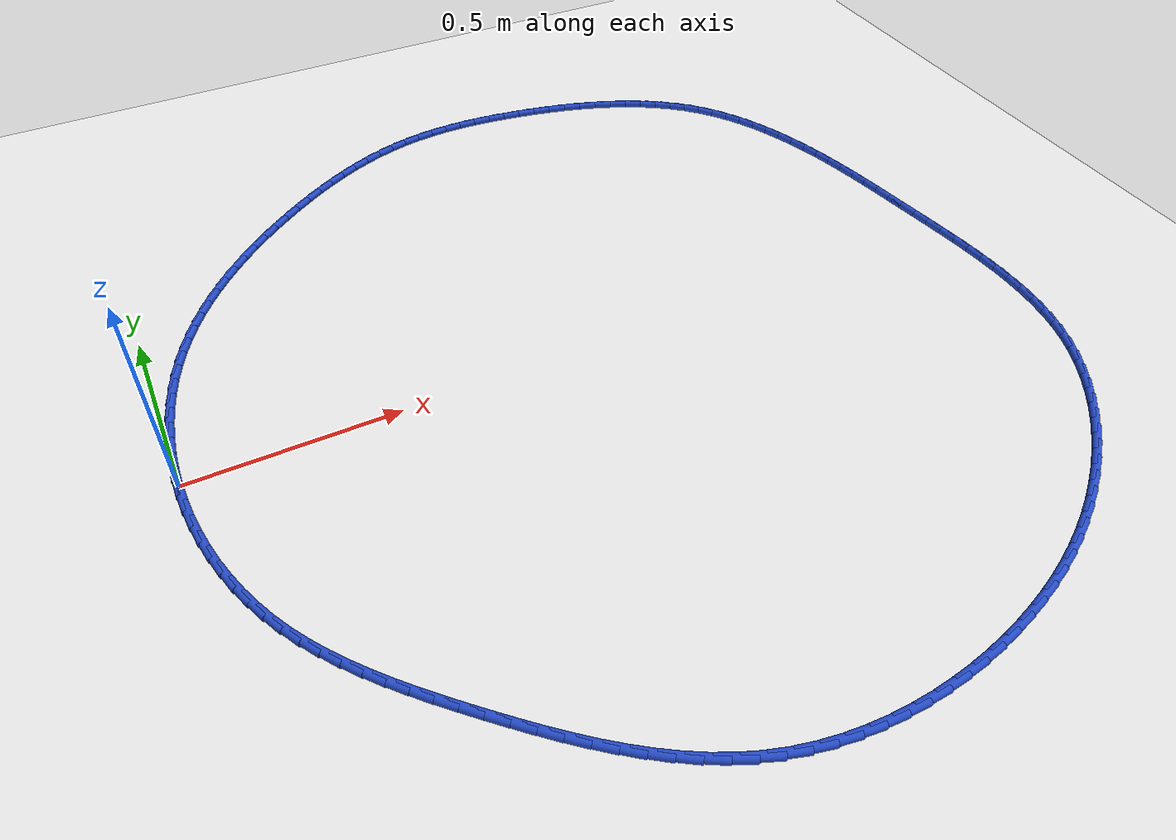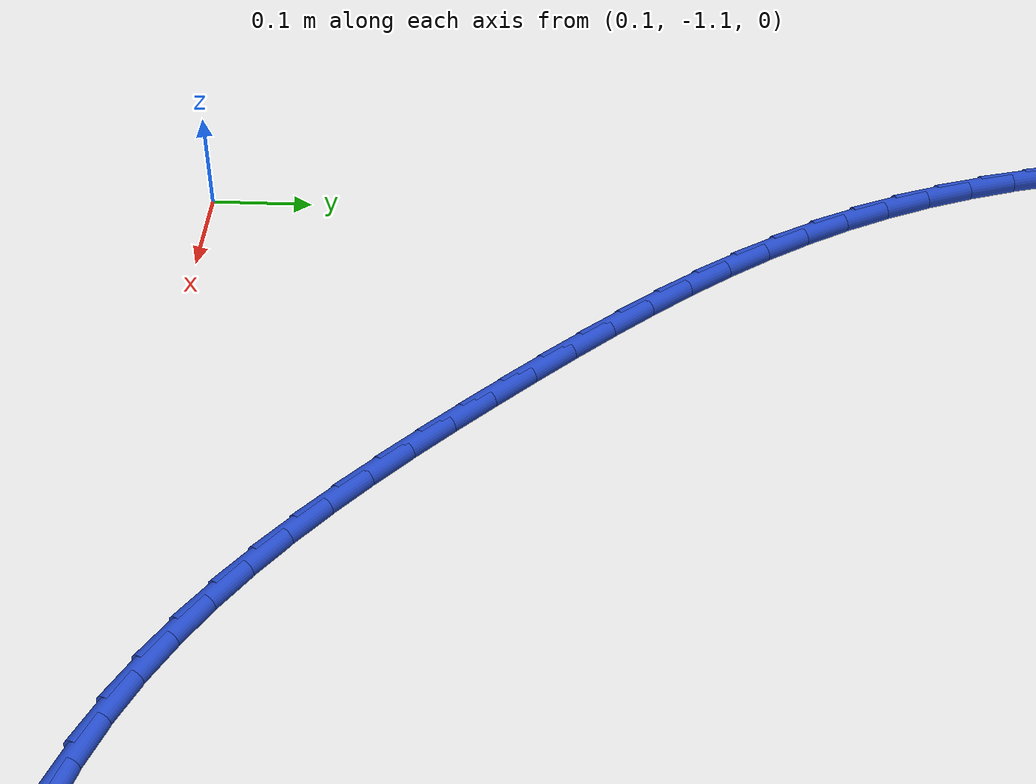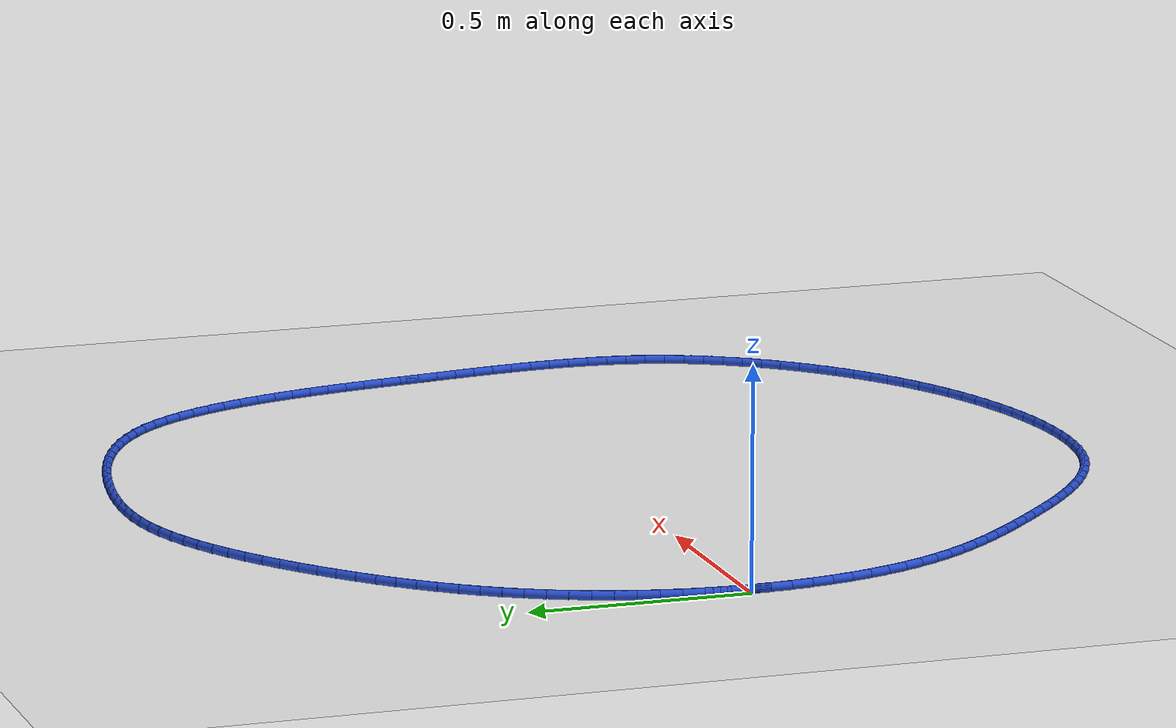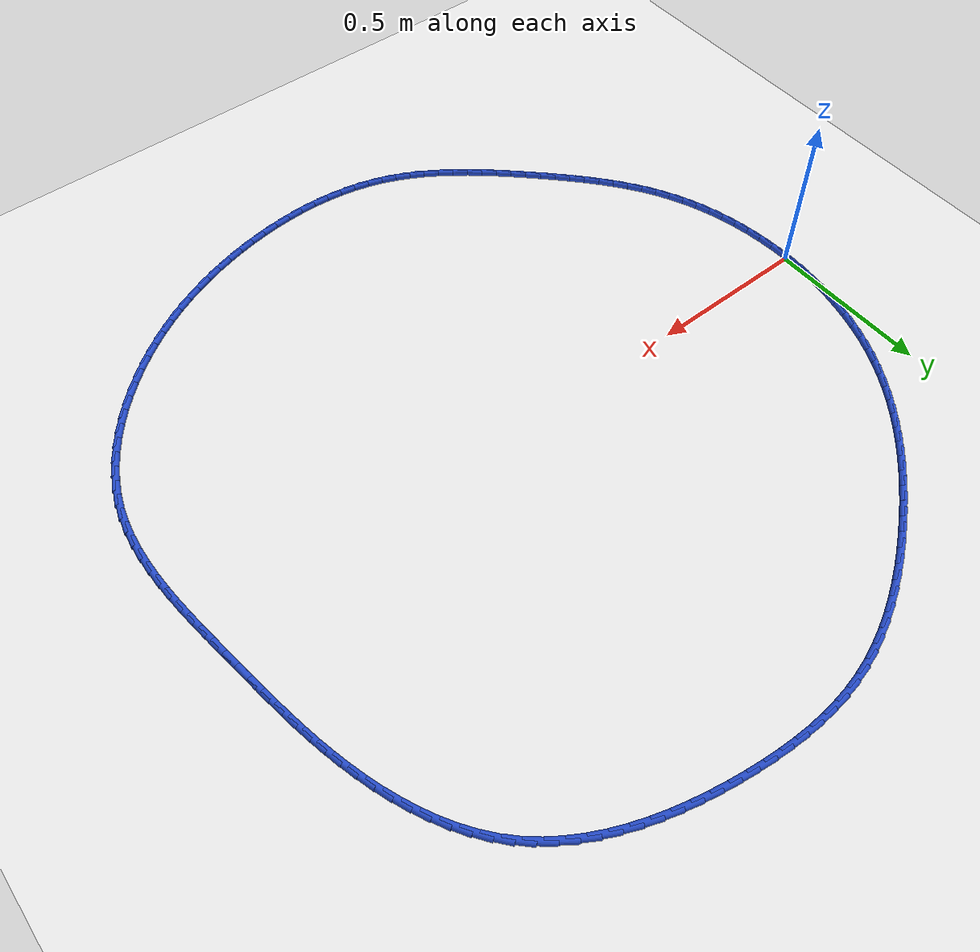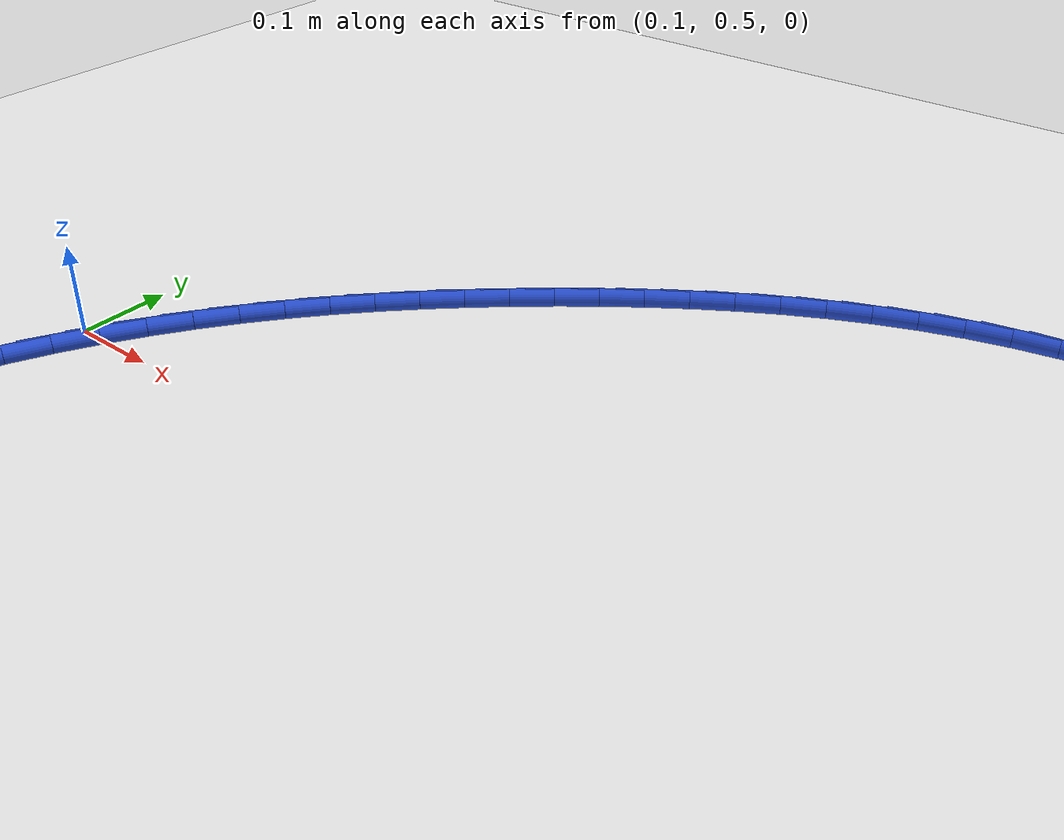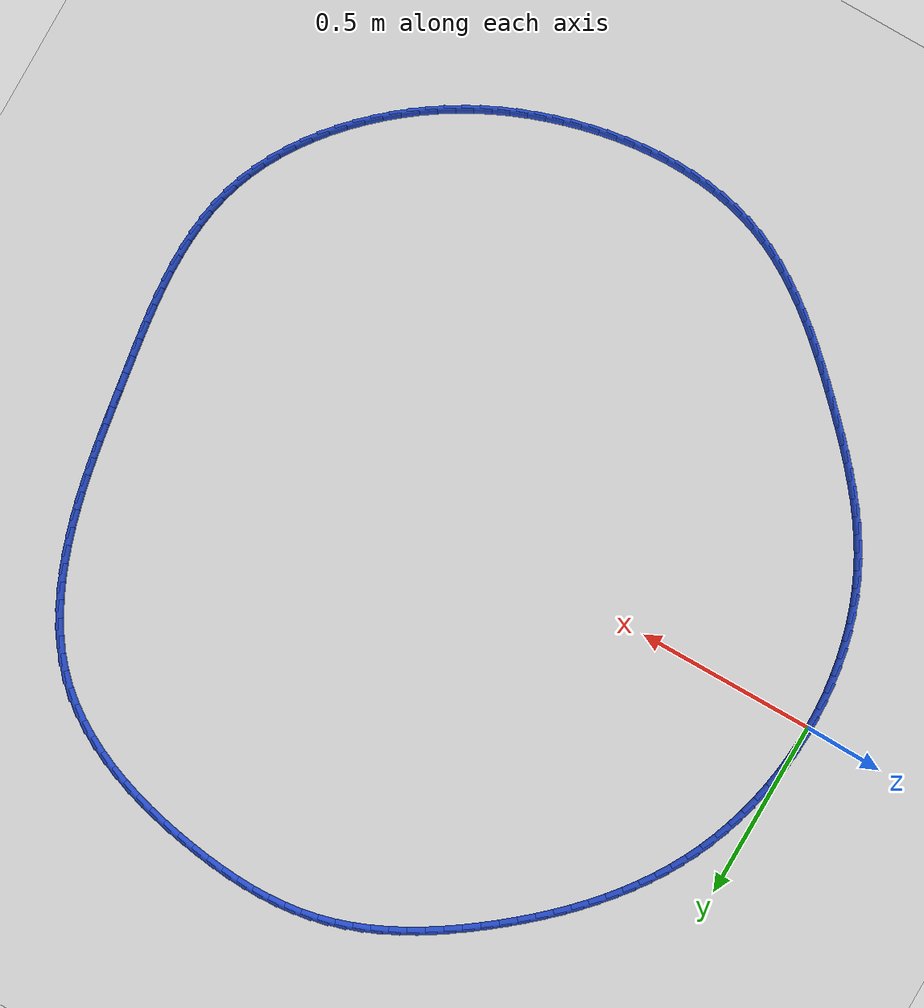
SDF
<sdf version="1.6">
 <world name="default">
  <light name="sun" type="directional">
   <pose>0 0 10 0 -0 0</pose>
   <diffuse>0.8 0.8 0.8 1</diffuse>
   <specular>0.2 0.2 0.2 1</specular>
   <attenuation>
    <range>1000</range>
    <constant>0.9</constant>
    <linear>0.01</linear>
    <quadratic>0.001</quadratic>
   </attenuation>
   <direction>-0.5 0.1 -0.9</direction>
  </light>
  <model name="ground_plane">
   <static>1</static>
   <link name="link">
    <collision name="collision">
     <geometry><plane><normal>0 0 1</normal><size>100 100</size></plane></geometry>
     <surface><friction><ode><mu>100</mu><mu2>50</mu2></ode></friction></surface>
    </collision>
    <visual name="visual">
     <cast_shadows>0</cast_shadows>
     <geometry><plane><normal>0 0 1</normal><size>100 100</size></plane></geometry>
     <material>
      <script><uri>file://media/materials/scripts/gazebo.material</uri><name>Gazebo/WhiteGlow</name></script>
     </material>
    </visual>
   </link>
  </model>
  <gravity>0 0 -9.8</gravity>
  <magnetic_field>6e-06 2.3e-05 -4.2e-05</magnetic_field>
  <atmosphere type="adiabatic"/>
  <physics name="default_physics" default="0" type="ode">
   <max_step_size>0.001</max_step_size>
   <real_time_factor>1</real_time_factor>
   <real_time_update_rate>1000</real_time_update_rate>
  </physics>
  <scene><ambient>0.4 0.4 0.4 1</ambient><background>0.7 0.7 0.7 1</background><shadows>1</shadows></scene>
  <spherical_coordinates>
   <surface_model>EARTH_WGS84</surface_model>
   <latitude_deg>0</latitude_deg>
   <longitude_deg>0</longitude_deg>
   <elevation>0</elevation>
   <heading_deg>0</heading_deg>
  </spherical_coordinates>
  <model name="line">
   <link name="link_0">
    <pose>-1.3877787807814457e-17 -2.7755575615628914e-17 0.01 0 1.57 1.5439862479537985</pose>
    <collision name="collision">
     <geometry><cylinder><radius>0.01</radius><length>0.08</length></cylinder></geometry>
    </collision>
    <visual name="visual">
     <material>
      <script><name>Gazebo/Blue</name><uri>file://media/materials/scripts/gazebo.material</uri></script>
     </material>
     <geometry><cylinder><radius>0.01</radius><length>0.08</length></cylinder></geometry>
    </visual>
   </link>
   <link name="link_1">
    <pose>0.0013000955071772464 0.04848117029403217 0.01 0 1.57 1.49732978394675</pose>
    <collision name="collision">
     <geometry><cylinder><radius>0.01</radius><length>0.08</length></cylinder></geometry>
    </collision>
    <visual name="visual">
     <material>
      <script><name>Gazebo/Blue</name><uri>file://media/materials/scripts/gazebo.material</uri></script>
     </material>
     <geometry><cylinder><radius>0.01</radius><length>0.08</length></cylinder></geometry>
    </visual>
   </link>
   <link name="link_2">
    <pose>0.004854775804561397 0.0967791110049405 0.01 0 1.57 1.450515364279473</pose>
    <collision name="collision">
     <geometry><cylinder><radius>0.01</radius><length>0.08</length></cylinder></geometry>
    </collision>
    <visual name="visual">
     <material>
      <script><name>Gazebo/Blue</name><uri>file://media/materials/scripts/gazebo.material</uri></script>
     </material>
     <geometry><cylinder><radius>0.01</radius><length>0.08</length></cylinder></geometry>
    </visual>
   </link>
   <link name="link_3">
    <pose>0.010655439018264075 0.1447722626850268 0.01 0 1.57 1.403393478930387</pose>
    <collision name="collision">
     <geometry><cylinder><radius>0.01</radius><length>0.08</length></cylinder></geometry>
    </collision>
    <visual name="visual">
     <material>
      <script><name>Gazebo/Blue</name><uri>file://media/materials/scripts/gazebo.material</uri></script>
     </material>
     <geometry><cylinder><radius>0.01</radius><length>0.08</length></cylinder></geometry>
    </visual>
   </link>
   <link name="link_4">
    <pose>0.018693483274396905 0.1923390658865928 0.01 0 1.57 1.35581536525314</pose>
    <collision name="collision">
     <geometry><cylinder><radius>0.01</radius><length>0.08</length></cylinder></geometry>
    </collision>
    <visual name="visual">
     <material>
      <script><name>Gazebo/Blue</name><uri>file://media/materials/scripts/gazebo.material</uri></script>
     </material>
     <geometry><cylinder><radius>0.01</radius><length>0.08</length></cylinder></geometry>
    </visual>
   </link>
   <link name="link_5">
    <pose>0.028960306699071535 0.23935796116194058 0.01 0 1.57 1.3076344582694799</pose>
    <collision name="collision">
     <geometry><cylinder><radius>0.01</radius><length>0.08</length></cylinder></geometry>
    </collision>
    <visual name="visual">
     <material>
      <script><name>Gazebo/Blue</name><uri>file://media/materials/scripts/gazebo.material</uri></script>
     </material>
     <geometry><cylinder><radius>0.01</radius><length>0.08</length></cylinder></geometry>
    </visual>
   </link>
   <link name="link_6">
    <pose>0.041447307418399575 0.2857073890633719 0.01 0 1.57 1.2587081270434302</pose>
    <collision name="collision">
     <geometry><cylinder><radius>0.01</radius><length>0.08</length></cylinder></geometry>
    </collision>
    <visual name="visual">
     <material>
      <script><name>Gazebo/Blue</name><uri>file://media/materials/scripts/gazebo.material</uri></script>
     </material>
     <geometry><cylinder><radius>0.01</radius><length>0.08</length></cylinder></geometry>
    </visual>
   </link>
   <link name="link_7">
    <pose>0.056145883558492655 0.33126579014318835 0.01 0 1.57 1.2088997947003792</pose>
    <collision name="collision">
     <geometry><cylinder><radius>0.01</radius><length>0.08</length></cylinder></geometry>
    </collision>
    <visual name="visual">
     <material>
      <script><name>Gazebo/Blue</name><uri>file://media/materials/scripts/gazebo.material</uri></script>
     </material>
     <geometry><cylinder><radius>0.01</radius><length>0.08</length></cylinder></geometry>
    </visual>
   </link>
   <link name="link_8">
    <pose>0.07304743324546242 0.3759116049536922 0.01 0 1.57 1.158081530618101</pose>
    <collision name="collision">
     <geometry><cylinder><radius>0.01</radius><length>0.08</length></cylinder></geometry>
    </collision>
    <visual name="visual">
     <material>
      <script><name>Gazebo/Blue</name><uri>file://media/materials/scripts/gazebo.material</uri></script>
     </material>
     <geometry><cylinder><radius>0.01</radius><length>0.08</length></cylinder></geometry>
    </visual>
   </link>
   <link name="link_9">
    <pose>0.09214335460542052 0.4195232740471851 0.01 0 1.57 1.1063028263556682</pose>
    <collision name="collision">
     <geometry><cylinder><radius>0.01</radius><length>0.08</length></cylinder></geometry>
    </collision>
    <visual name="visual">
     <material>
      <script><name>Gazebo/Blue</name><uri>file://media/materials/scripts/gazebo.material</uri></script>
     </material>
     <geometry><cylinder><radius>0.01</radius><length>0.08</length></cylinder></geometry>
    </visual>
   </link>
   <link name="link_10">
    <pose>0.1134197853109428 0.46198629966658694 0.01 0 1.57 1.0554651047905392</pose>
    <collision name="collision">
     <geometry><cylinder><radius>0.01</radius><length>0.08</length></cylinder></geometry>
    </collision>
    <visual name="visual">
     <material>
      <script><name>Gazebo/Blue</name><uri>file://media/materials/scripts/gazebo.material</uri></script>
     </material>
     <geometry><cylinder><radius>0.01</radius><length>0.08</length></cylinder></geometry>
    </visual>
   </link>
   <link name="link_11">
    <pose>0.13680132337337977 0.503268795572125 0.01 0 1.57 1.0069436426508978</pose>
    <collision name="collision">
     <geometry><cylinder><radius>0.01</radius><length>0.08</length></cylinder></geometry>
    </collision>
    <visual name="visual">
     <material>
      <script><name>Gazebo/Blue</name><uri>file://media/materials/scripts/gazebo.material</uri></script>
     </material>
     <geometry><cylinder><radius>0.01</radius><length>0.08</length></cylinder></geometry>
    </visual>
   </link>
   <link name="link_12">
    <pose>0.1621726793115521 0.543392420932205 0.01 0 1.57 0.9608611292791025</pose>
    <collision name="collision">
     <geometry><cylinder><radius>0.01</radius><length>0.08</length></cylinder></geometry>
    </collision>
    <visual name="visual">
     <material>
      <script><name>Gazebo/Blue</name><uri>file://media/materials/scripts/gazebo.material</uri></script>
     </material>
     <geometry><cylinder><radius>0.01</radius><length>0.08</length></cylinder></geometry>
    </visual>
   </link>
   <link name="link_13">
    <pose>0.18941789051490968 0.5823797385314952 0.01 0 1.57 0.9172676235444962</pose>
    <collision name="collision">
     <geometry><cylinder><radius>0.01</radius><length>0.08</length></cylinder></geometry>
    </collision>
    <visual name="visual">
     <material>
      <script><name>Gazebo/Blue</name><uri>file://media/materials/scripts/gazebo.material</uri></script>
     </material>
     <geometry><cylinder><radius>0.01</radius><length>0.08</length></cylinder></geometry>
    </visual>
   </link>
   <link name="link_14">
    <pose>0.21842099437290244 0.6202533111546634 0.01 0 1.57 0.8761697022894857</pose>
    <collision name="collision">
     <geometry><cylinder><radius>0.01</radius><length>0.08</length></cylinder></geometry>
    </collision>
    <visual name="visual">
     <material>
      <script><name>Gazebo/Blue</name><uri>file://media/materials/scripts/gazebo.material</uri></script>
     </material>
     <geometry><cylinder><radius>0.01</radius><length>0.08</length></cylinder></geometry>
    </visual>
   </link>
   <link name="link_15">
    <pose>0.24906602827498026 0.6570357015863781 0.01 0 1.57 0.8375388492381575</pose>
    <collision name="collision">
     <geometry><cylinder><radius>0.01</radius><length>0.08</length></cylinder></geometry>
    </collision>
    <visual name="visual">
     <material>
      <script><name>Gazebo/Blue</name><uri>file://media/materials/scripts/gazebo.material</uri></script>
     </material>
     <geometry><cylinder><radius>0.01</radius><length>0.08</length></cylinder></geometry>
    </visual>
   </link>
   <link name="link_16">
    <pose>0.28123702961059305 0.6927494726113071 0.01 0 1.57 0.801319581556434</pose>
    <collision name="collision">
     <geometry><cylinder><radius>0.01</radius><length>0.08</length></cylinder></geometry>
    </collision>
    <visual name="visual">
     <material>
      <script><name>Gazebo/Blue</name><uri>file://media/materials/scripts/gazebo.material</uri></script>
     </material>
     <geometry><cylinder><radius>0.01</radius><length>0.08</length></cylinder></geometry>
    </visual>
   </link>
   <link name="link_17">
    <pose>0.31481803576919076 0.7274171870141186 0.01 0 1.57 0.767436859030929</pose>
    <collision name="collision">
     <geometry><cylinder><radius>0.01</radius><length>0.08</length></cylinder></geometry>
    </collision>
    <visual name="visual">
     <material>
      <script><name>Gazebo/Blue</name><uri>file://media/materials/scripts/gazebo.material</uri></script>
     </material>
     <geometry><cylinder><radius>0.01</radius><length>0.08</length></cylinder></geometry>
    </visual>
   </link>
   <link name="link_18">
    <pose>0.3496930841402231 0.7610614075794808 0.01 0 1.57 0.7358025313461442</pose>
    <collision name="collision">
     <geometry><cylinder><radius>0.01</radius><length>0.08</length></cylinder></geometry>
    </collision>
    <visual name="visual">
     <material>
      <script><name>Gazebo/Blue</name><uri>file://media/materials/scripts/gazebo.material</uri></script>
     </material>
     <geometry><cylinder><radius>0.01</radius><length>0.08</length></cylinder></geometry>
    </visual>
   </link>
   <link name="link_19">
    <pose>0.3857462121131401 0.7937046970920614 0.01 0 1.57 0.7063207410016091</pose>
    <collision name="collision">
     <geometry><cylinder><radius>0.01</radius><length>0.08</length></cylinder></geometry>
    </collision>
    <visual name="visual">
     <material>
      <script><name>Gazebo/Blue</name><uri>file://media/materials/scripts/gazebo.material</uri></script>
     </material>
     <geometry><cylinder><radius>0.01</radius><length>0.08</length></cylinder></geometry>
    </visual>
   </link>
   <link name="link_20">
    <pose>0.42286145707739187 0.8253696183365292 0.01 0 1.57 0.6788923109221581</pose>
    <collision name="collision">
     <geometry><cylinder><radius>0.01</radius><length>0.08</length></cylinder></geometry>
    </collision>
    <visual name="visual">
     <material>
      <script><name>Gazebo/Blue</name><uri>file://media/materials/scripts/gazebo.material</uri></script>
     </material>
     <geometry><cylinder><radius>0.01</radius><length>0.08</length></cylinder></geometry>
    </visual>
   </link>
   <link name="link_21">
    <pose>0.4609228564224279 0.8560787340975516 0.01 0 1.57 0.6528561740474497</pose>
    <collision name="collision">
     <geometry><cylinder><radius>0.01</radius><length>0.08</length></cylinder></geometry>
    </collision>
    <visual name="visual">
     <material>
      <script><name>Gazebo/Blue</name><uri>file://media/materials/scripts/gazebo.material</uri></script>
     </material>
     <geometry><cylinder><radius>0.01</radius><length>0.08</length></cylinder></geometry>
    </visual>
   </link>
   <link name="link_22">
    <pose>0.4998251105921384 0.8858281050375019 0.01 0 1.57 0.6246889999365038</pose>
    <collision name="collision">
     <geometry><cylinder><radius>0.01</radius><length>0.08</length></cylinder></geometry>
    </collision>
    <visual name="visual">
     <material>
      <script><name>Gazebo/Blue</name><uri>file://media/materials/scripts/gazebo.material</uri></script>
     </material>
     <geometry><cylinder><radius>0.01</radius><length>0.08</length></cylinder></geometry>
    </visual>
   </link>
   <link name="link_23">
    <pose>0.5395272795234832 0.9144538317279781 0.01 0 1.57 0.5929173329271502</pose>
    <collision name="collision">
     <geometry><cylinder><radius>0.01</radius><length>0.08</length></cylinder></geometry>
    </collision>
    <visual name="visual">
     <material>
      <script><name>Gazebo/Blue</name><uri>file://media/materials/scripts/gazebo.material</uri></script>
     </material>
     <geometry><cylinder><radius>0.01</radius><length>0.08</length></cylinder></geometry>
    </visual>
   </link>
   <link name="link_24">
    <pose>0.5800124497341687 0.9417322987009699 0.01 0 1.57 0.5572982903849244</pose>
    <collision name="collision">
     <geometry><cylinder><radius>0.01</radius><length>0.08</length></cylinder></geometry>
    </collision>
    <visual name="visual">
     <material>
      <script><name>Gazebo/Blue</name><uri>file://media/materials/scripts/gazebo.material</uri></script>
     </material>
     <geometry><cylinder><radius>0.01</radius><length>0.08</length></cylinder></geometry>
    </visual>
   </link>
   <link name="link_25">
    <pose>0.6212637490057964 0.9674397879305382 0.01 0 1.57 0.5175737755736487</pose>
    <collision name="collision">
     <geometry><cylinder><radius>0.01</radius><length>0.08</length></cylinder></geometry>
    </collision>
    <visual name="visual">
     <material>
      <script><name>Gazebo/Blue</name><uri>file://media/materials/scripts/gazebo.material</uri></script>
     </material>
     <geometry><cylinder><radius>0.01</radius><length>0.08</length></cylinder></geometry>
    </visual>
   </link>
   <link name="link_26">
    <pose>0.6632643051199675 0.991352581390743 0.01 0 1.57 0.4734816439089766</pose>
    <collision name="collision">
     <geometry><cylinder><radius>0.01</radius><length>0.08</length></cylinder></geometry>
    </collision>
    <visual name="visual">
     <material>
      <script><name>Gazebo/Blue</name><uri>file://media/materials/scripts/gazebo.material</uri></script>
     </material>
     <geometry><cylinder><radius>0.01</radius><length>0.08</length></cylinder></geometry>
    </visual>
   </link>
   <link name="link_27">
    <pose>0.7059972458582832 1.0132469610556454 0.01 0 1.57 0.42477475289719163</pose>
    <collision name="collision">
     <geometry><cylinder><radius>0.01</radius><length>0.08</length></cylinder></geometry>
    </collision>
    <visual name="visual">
     <material>
      <script><name>Gazebo/Blue</name><uri>file://media/materials/scripts/gazebo.material</uri></script>
     </material>
     <geometry><cylinder><radius>0.01</radius><length>0.08</length></cylinder></geometry>
    </visual>
   </link>
   <link name="link_28">
    <pose>0.7494456990023451 1.0328992088993056 0.01 0 1.57 0.3712470565876326</pose>
    <collision name="collision">
     <geometry><cylinder><radius>0.01</radius><length>0.08</length></cylinder></geometry>
    </collision>
    <visual name="visual">
     <material>
      <script><name>Gazebo/Blue</name><uri>file://media/materials/scripts/gazebo.material</uri></script>
     </material>
     <geometry><cylinder><radius>0.01</radius><length>0.08</length></cylinder></geometry>
    </visual>
   </link>
   <link name="link_29">
    <pose>0.7935927923337546 1.050085606895784 0.01 0 1.57 0.31276744081775637</pose>
    <collision name="collision">
     <geometry><cylinder><radius>0.01</radius><length>0.08</length></cylinder></geometry>
    </collision>
    <visual name="visual">
     <material>
      <script><name>Gazebo/Blue</name><uri>file://media/materials/scripts/gazebo.material</uri></script>
     </material>
     <geometry><cylinder><radius>0.01</radius><length>0.08</length></cylinder></geometry>
    </visual>
   </link>
   <link name="link_30">
    <pose>0.8384216536341128 1.0645824370191415 0.01 0 1.57 0.24932057655634146</pose>
    <collision name="collision">
     <geometry><cylinder><radius>0.01</radius><length>0.08</length></cylinder></geometry>
    </collision>
    <visual name="visual">
     <material>
      <script><name>Gazebo/Blue</name><uri>file://media/materials/scripts/gazebo.material</uri></script>
     </material>
     <geometry><cylinder><radius>0.01</radius><length>0.08</length></cylinder></geometry>
    </visual>
   </link>
   <link name="link_31">
    <pose>0.8839154106850214 1.0761659812434385 0.01 0 1.57 0.18257393777778924</pose>
    <collision name="collision">
     <geometry><cylinder><radius>0.01</radius><length>0.08</length></cylinder></geometry>
    </collision>
    <visual name="visual">
     <material>
      <script><name>Gazebo/Blue</name><uri>file://media/materials/scripts/gazebo.material</uri></script>
     </material>
     <geometry><cylinder><radius>0.01</radius><length>0.08</length></cylinder></geometry>
    </visual>
   </link>
   <link name="link_32">
    <pose>0.9300488244824214 1.0846835910959602 0.01 0 1.57 0.11912959833834877</pose>
    <collision name="collision">
     <geometry><cylinder><radius>0.01</radius><length>0.08</length></cylinder></geometry>
    </collision>
    <visual name="visual">
     <material>
      <script><name>Gazebo/Blue</name><uri>file://media/materials/scripts/gazebo.material</uri></script>
     </material>
     <geometry><cylinder><radius>0.01</radius><length>0.08</length></cylinder></geometry>
    </visual>
   </link>
   <link name="link_33">
    <pose>0.9767622328994956 1.090275016649207 0.01 0 1.57 0.060913125359275754</pose>
    <collision name="collision">
     <geometry><cylinder><radius>0.01</radius><length>0.08</length></cylinder></geometry>
    </collision>
    <visual name="visual">
     <material>
      <script><name>Gazebo/Blue</name><uri>file://media/materials/scripts/gazebo.material</uri></script>
     </material>
     <geometry><cylinder><radius>0.01</radius><length>0.08</length></cylinder></geometry>
    </visual>
   </link>
   <link name="link_34">
    <pose>1.023987122246294 1.093155195349033 0.01 0 1.57 0.00805282810111793</pose>
    <collision name="collision">
     <geometry><cylinder><radius>0.01</radius><length>0.08</length></cylinder></geometry>
    </collision>
    <visual name="visual">
     <material>
      <script><name>Gazebo/Blue</name><uri>file://media/materials/scripts/gazebo.material</uri></script>
     </material>
     <geometry><cylinder><radius>0.01</radius><length>0.08</length></cylinder></geometry>
    </visual>
   </link>
   <link name="link_35">
    <pose>1.071654978825745 1.093539064701777 0.01 0 1.57 -0.039475968621177415</pose>
    <collision name="collision">
     <geometry><cylinder><radius>0.01</radius><length>0.08</length></cylinder></geometry>
    </collision>
    <visual name="visual">
     <material>
      <script><name>Gazebo/Blue</name><uri>file://media/materials/scripts/gazebo.material</uri></script>
     </material>
     <geometry><cylinder><radius>0.01</radius><length>0.08</length></cylinder></geometry>
    </visual>
   </link>
   <link name="link_36">
    <pose>1.1196972889407786 1.091641562213777 0.01 0 1.57 -0.08180421731407035</pose>
    <collision name="collision">
     <geometry><cylinder><radius>0.01</radius><length>0.08</length></cylinder></geometry>
    </collision>
    <visual name="visual">
     <material>
      <script><name>Gazebo/Blue</name><uri>file://media/materials/scripts/gazebo.material</uri></script>
     </material>
     <geometry><cylinder><radius>0.01</radius><length>0.08</length></cylinder></geometry>
    </visual>
   </link>
   <link name="link_37">
    <pose>1.1680455388943238 1.0876776253913716 0.01 0 1.57 -0.11912765942808072</pose>
    <collision name="collision">
     <geometry><cylinder><radius>0.01</radius><length>0.08</length></cylinder></geometry>
    </collision>
    <visual name="visual">
     <material>
      <script><name>Gazebo/Blue</name><uri>file://media/materials/scripts/gazebo.material</uri></script>
     </material>
     <geometry><cylinder><radius>0.01</radius><length>0.08</length></cylinder></geometry>
    </visual>
   </link>
   <link name="link_38">
    <pose>1.2166312149893093 1.081862191740899 0.01 0 1.57 -0.15167389560832728</pose>
    <collision name="collision">
     <geometry><cylinder><radius>0.01</radius><length>0.08</length></cylinder></geometry>
    </collision>
    <visual name="visual">
     <material>
      <script><name>Gazebo/Blue</name><uri>file://media/materials/scripts/gazebo.material</uri></script>
     </material>
     <geometry><cylinder><radius>0.01</radius><length>0.08</length></cylinder></geometry>
    </visual>
   </link>
   <link name="link_39">
    <pose>1.2653857844287881 1.0744101638715478 0.01 0 1.57 -0.1812845392434964</pose>
    <collision name="collision">
     <geometry><cylinder><radius>0.01</radius><length>0.08</length></cylinder></geometry>
    </collision>
    <visual name="visual">
     <material>
      <script><name>Gazebo/Blue</name><uri>file://media/materials/scripts/gazebo.material</uri></script>
     </material>
     <geometry><cylinder><radius>0.01</radius><length>0.08</length></cylinder></geometry>
    </visual>
   </link>
   <link name="link_40">
    <pose>1.3142003050210591 1.065462612882846 0.01 0 1.57 -0.21323153890450583</pose>
    <collision name="collision">
     <geometry><cylinder><radius>0.01</radius><length>0.08</length></cylinder></geometry>
    </collision>
    <visual name="visual">
     <material>
      <script><name>Gazebo/Blue</name><uri>file://media/materials/scripts/gazebo.material</uri></script>
     </material>
     <geometry><cylinder><radius>0.01</radius><length>0.08</length></cylinder></geometry>
    </visual>
   </link>
   <link name="link_41">
    <pose>1.3628401442285534 1.0549309625845849 0.01 0 1.57 -0.2488271544679976</pose>
    <collision name="collision">
     <geometry><cylinder><radius>0.01</radius><length>0.08</length></cylinder></geometry>
    </collision>
    <visual name="visual">
     <material>
      <script><name>Gazebo/Blue</name><uri>file://media/materials/scripts/gazebo.material</uri></script>
     </material>
     <geometry><cylinder><radius>0.01</radius><length>0.08</length></cylinder></geometry>
    </visual>
   </link>
   <link name="link_42">
    <pose>1.4110463025242534 1.0426821161589201 0.01 0 1.57 -0.28846309744115495</pose>
    <collision name="collision">
     <geometry><cylinder><radius>0.01</radius><length>0.08</length></cylinder></geometry>
    </collision>
    <visual name="visual">
     <material>
      <script><name>Gazebo/Blue</name><uri>file://media/materials/scripts/gazebo.material</uri></script>
     </material>
     <geometry><cylinder><radius>0.01</radius><length>0.08</length></cylinder></geometry>
    </visual>
   </link>
   <link name="link_43">
    <pose>1.4585597803811412 1.028582976788006 0.01 0 1.57 -0.3325725751890111</pose>
    <collision name="collision">
     <geometry><cylinder><radius>0.01</radius><length>0.08</length></cylinder></geometry>
    </collision>
    <visual name="visual">
     <material>
      <script><name>Gazebo/Blue</name><uri>file://media/materials/scripts/gazebo.material</uri></script>
     </material>
     <geometry><cylinder><radius>0.01</radius><length>0.08</length></cylinder></geometry>
    </visual>
   </link>
   <link name="link_44">
    <pose>1.5051215782722 1.0125004476539972 0.01 0 1.57 -0.38161919347276557</pose>
    <collision name="collision">
     <geometry><cylinder><radius>0.01</radius><length>0.08</length></cylinder></geometry>
    </collision>
    <visual name="visual">
     <material>
      <script><name>Gazebo/Blue</name><uri>file://media/materials/scripts/gazebo.material</uri></script>
     </material>
     <geometry><cylinder><radius>0.01</radius><length>0.08</length></cylinder></geometry>
    </visual>
   </link>
   <link name="link_45">
    <pose>1.5504726966704117 0.994301431939048 0.01 0 1.57 -0.4360767356400772</pose>
    <collision name="collision">
     <geometry><cylinder><radius>0.01</radius><length>0.08</length></cylinder></geometry>
    </collision>
    <visual name="visual">
     <material>
      <script><name>Gazebo/Blue</name><uri>file://media/materials/scripts/gazebo.material</uri></script>
     </material>
     <geometry><cylinder><radius>0.01</radius><length>0.08</length></cylinder></geometry>
    </visual>
   </link>
   <link name="link_46">
    <pose>1.5943541360487585 0.9738528328253133 0.01 0 1.57 -0.49639586184257994</pose>
    <collision name="collision">
     <geometry><cylinder><radius>0.01</radius><length>0.08</length></cylinder></geometry>
    </collision>
    <visual name="visual">
     <material>
      <script><name>Gazebo/Blue</name><uri>file://media/materials/scripts/gazebo.material</uri></script>
     </material>
     <geometry><cylinder><radius>0.01</radius><length>0.08</length></cylinder></geometry>
    </visual>
   </link>
   <link name="link_47">
    <pose>1.6365068968802234 0.9510215534949483 0.01 0 1.57 -0.5629537376569442</pose>
    <collision name="collision">
     <geometry><cylinder><radius>0.01</radius><length>0.08</length></cylinder></geometry>
    </collision>
    <visual name="visual">
     <material>
      <script><name>Gazebo/Blue</name><uri>file://media/materials/scripts/gazebo.material</uri></script>
     </material>
     <geometry><cylinder><radius>0.01</radius><length>0.08</length></cylinder></geometry>
    </visual>
   </link>
   <link name="link_48">
    <pose>1.676671979637788 0.9256744971301065 0.01 0 1.57 -0.6359841325285005</pose>
    <collision name="collision">
     <geometry><cylinder><radius>0.01</radius><length>0.08</length></cylinder></geometry>
    </collision>
    <visual name="visual">
     <material>
      <script><name>Gazebo/Blue</name><uri>file://media/materials/scripts/gazebo.material</uri></script>
     </material>
     <geometry><cylinder><radius>0.01</radius><length>0.08</length></cylinder></geometry>
    </visual>
   </link>
   <link name="link_49">
    <pose>1.714590384794435 0.8976785669129436 0.01 0 1.57 -0.7154898642995443</pose>
    <collision name="collision">
     <geometry><cylinder><radius>0.01</radius><length>0.08</length></cylinder></geometry>
    </collision>
    <visual name="visual">
     <material>
      <script><name>Gazebo/Blue</name><uri>file://media/materials/scripts/gazebo.material</uri></script>
     </material>
     <geometry><cylinder><radius>0.01</radius><length>0.08</length></cylinder></geometry>
    </visual>
   </link>
   <link name="link_50">
    <pose>1.750003112823147 0.8669006660256134 0.01 0 1.57 -0.8010830907051544</pose>
    <collision name="collision">
     <geometry><cylinder><radius>0.01</radius><length>0.08</length></cylinder></geometry>
    </collision>
    <visual name="visual">
     <material>
      <script><name>Gazebo/Blue</name><uri>file://media/materials/scripts/gazebo.material</uri></script>
     </material>
     <geometry><cylinder><radius>0.01</radius><length>0.08</length></cylinder></geometry>
    </visual>
   </link>
   <link name="link_51">
    <pose>1.7826530891976295 0.8332100570532648 0.01 0 1.57 -0.8872848594665548</pose>
    <collision name="collision">
     <geometry><cylinder><radius>0.01</radius><length>0.08</length></cylinder></geometry>
    </collision>
    <visual name="visual">
     <material>
      <script><name>Gazebo/Blue</name><uri>file://media/materials/scripts/gazebo.material</uri></script>
     </material>
     <geometry><cylinder><radius>0.01</radius><length>0.08</length></cylinder></geometry>
    </visual>
   </link>
   <link name="link_52">
    <pose>1.8124279688652252 0.7966533922044512 0.01 0 1.57 -0.9656628378489084</pose>
    <collision name="collision">
     <geometry><cylinder><radius>0.01</radius><length>0.08</length></cylinder></geometry>
    </collision>
    <visual name="visual">
     <material>
      <script><name>Gazebo/Blue</name><uri>file://media/materials/scripts/gazebo.material</uri></script>
     </material>
     <geometry><cylinder><radius>0.01</radius><length>0.08</length></cylinder></geometry>
    </visual>
   </link>
   <link name="link_53">
    <pose>1.8394583853857267 0.7575751336878254 0.01 0 1.57 -1.0356783595167642</pose>
    <collision name="collision">
     <geometry><cylinder><radius>0.01</radius><length>0.08</length></cylinder></geometry>
    </collision>
    <visual name="visual">
     <material>
      <script><name>Gazebo/Blue</name><uri>file://media/materials/scripts/gazebo.material</uri></script>
     </material>
     <geometry><cylinder><radius>0.01</radius><length>0.08</length></cylinder></geometry>
    </visual>
   </link>
   <link name="link_54">
    <pose>1.8638982161848177 0.7163482328684839 0.01 0 1.57 -1.097856614247655</pose>
    <collision name="collision">
     <geometry><cylinder><radius>0.01</radius><length>0.08</length></cylinder></geometry>
    </collision>
    <visual name="visual">
     <material>
      <script><name>Gazebo/Blue</name><uri>file://media/materials/scripts/gazebo.material</uri></script>
     </material>
     <geometry><cylinder><radius>0.01</radius><length>0.08</length></cylinder></geometry>
    </visual>
   </link>
   <link name="link_55">
    <pose>1.8859013386881784 0.6733456411115235 0.01 0 1.57 -1.1528618450016284</pose>
    <collision name="collision">
     <geometry><cylinder><radius>0.01</radius><length>0.08</length></cylinder></geometry>
    </collision>
    <visual name="visual">
     <material>
      <script><name>Gazebo/Blue</name><uri>file://media/materials/scripts/gazebo.material</uri></script>
     </material>
     <geometry><cylinder><radius>0.01</radius><length>0.08</length></cylinder></geometry>
    </visual>
   </link>
   <link name="link_56">
    <pose>1.905621630321493 0.6289403097820422 0.01 0 1.57 -1.201394719967363</pose>
    <collision name="collision">
     <geometry><cylinder><radius>0.01</radius><length>0.08</length></cylinder></geometry>
    </collision>
    <visual name="visual">
     <material>
      <script><name>Gazebo/Blue</name><uri>file://media/materials/scripts/gazebo.material</uri></script>
     </material>
     <geometry><cylinder><radius>0.01</radius><length>0.08</length></cylinder></geometry>
    </visual>
   </link>
   <link name="link_57">
    <pose>1.9232129685104424 0.5835051902451361 0.01 0 1.57 -1.244127885930229</pose>
    <collision name="collision">
     <geometry><cylinder><radius>0.01</radius><length>0.08</length></cylinder></geometry>
    </collision>
    <visual name="visual">
     <material>
      <script><name>Gazebo/Blue</name><uri>file://media/materials/scripts/gazebo.material</uri></script>
     </material>
     <geometry><cylinder><radius>0.01</radius><length>0.08</length></cylinder></geometry>
    </visual>
   </link>
   <link name="link_58">
    <pose>1.9388292306807102 0.5374132338659031 0.01 0 1.57 -1.2816702100760788</pose>
    <collision name="collision">
     <geometry><cylinder><radius>0.01</radius><length>0.08</length></cylinder></geometry>
    </collision>
    <visual name="visual">
     <material>
      <script><name>Gazebo/Blue</name><uri>file://media/materials/scripts/gazebo.material</uri></script>
     </material>
     <geometry><cylinder><radius>0.01</radius><length>0.08</length></cylinder></geometry>
    </visual>
   </link>
   <link name="link_59">
    <pose>1.9526243485189254 0.4910370620126329 0.01 0 1.57 -1.3147629024589147</pose>
    <collision name="collision">
     <geometry><cylinder><radius>0.01</radius><length>0.08</length></cylinder></geometry>
    </collision>
    <visual name="visual">
     <material>
      <script><name>Gazebo/Blue</name><uri>file://media/materials/scripts/gazebo.material</uri></script>
     </material>
     <geometry><cylinder><radius>0.01</radius><length>0.08</length></cylinder></geometry>
    </visual>
   </link>
   <link name="link_60">
    <pose>1.9647704164333546 0.4446388365008921 0.01 0 1.57 -1.3440114351240888</pose>
    <collision name="collision">
     <geometry><cylinder><radius>0.01</radius><length>0.08</length></cylinder></geometry>
    </collision>
    <visual name="visual">
     <material>
      <script><name>Gazebo/Blue</name><uri>file://media/materials/scripts/gazebo.material</uri></script>
     </material>
     <geometry><cylinder><radius>0.01</radius><length>0.08</length></cylinder></geometry>
    </visual>
   </link>
   <link name="link_61">
    <pose>1.9754839486207705 0.3982105729605267 0.01 0 1.57 -1.3692111294587208</pose>
    <collision name="collision">
     <geometry><cylinder><radius>0.01</radius><length>0.08</length></cylinder></geometry>
    </collision>
    <visual name="visual">
     <material>
      <script><name>Gazebo/Blue</name><uri>file://media/materials/scripts/gazebo.material</uri></script>
     </material>
     <geometry><cylinder><radius>0.01</radius><length>0.08</length></cylinder></geometry>
    </visual>
   </link>
   <link name="link_62">
    <pose>1.9849881238591265 0.3517037552844068 0.01 0 1.57 -1.3901311577646343</pose>
    <collision name="collision">
     <geometry><cylinder><radius>0.01</radius><length>0.08</length></cylinder></geometry>
    </collision>
    <visual name="visual">
     <material>
      <script><name>Gazebo/Blue</name><uri>file://media/materials/scripts/gazebo.material</uri></script>
     </material>
     <geometry><cylinder><radius>0.01</radius><length>0.08</length></cylinder></geometry>
    </visual>
   </link>
   <link name="link_63">
    <pose>1.9935061209263756 0.30506986736540104 0.01 0 1.57 -1.4066160370039393</pose>
    <collision name="collision">
     <geometry><cylinder><radius>0.01</radius><length>0.08</length></cylinder></geometry>
    </collision>
    <visual name="visual">
     <material>
      <script><name>Gazebo/Blue</name><uri>file://media/materials/scripts/gazebo.material</uri></script>
     </material>
     <geometry><cylinder><radius>0.01</radius><length>0.08</length></cylinder></geometry>
    </visual>
   </link>
   <link name="link_64">
    <pose>2.0012611186004707 0.25826039309637966 0.01 0 1.57 -1.4185781630623908</pose>
    <collision name="collision">
     <geometry><cylinder><radius>0.01</radius><length>0.08</length></cylinder></geometry>
    </collision>
    <visual name="visual">
     <material>
      <script><name>Gazebo/Blue</name><uri>file://media/materials/scripts/gazebo.material</uri></script>
     </material>
     <geometry><cylinder><radius>0.01</radius><length>0.08</length></cylinder></geometry>
    </visual>
   </link>
   <link name="link_65">
    <pose>2.0084762956593654 0.2112268163702114 0.01 0 1.57 -1.4259897261282055</pose>
    <collision name="collision">
     <geometry><cylinder><radius>0.01</radius><length>0.08</length></cylinder></geometry>
    </collision>
    <visual name="visual">
     <material>
      <script><name>Gazebo/Blue</name><uri>file://media/materials/scripts/gazebo.material</uri></script>
     </material>
     <geometry><cylinder><radius>0.01</radius><length>0.08</length></cylinder></geometry>
    </visual>
   </link>
   <link name="link_66">
    <pose>2.015374830881012 0.1639206210797652 0.01 0 1.57 -1.428875241439571</pose>
    <collision name="collision">
     <geometry><cylinder><radius>0.01</radius><length>0.08</length></cylinder></geometry>
    </collision>
    <visual name="visual">
     <material>
      <script><name>Gazebo/Blue</name><uri>file://media/materials/scripts/gazebo.material</uri></script>
     </material>
     <geometry><cylinder><radius>0.01</radius><length>0.08</length></cylinder></geometry>
    </visual>
   </link>
   <link name="link_67">
    <pose>2.0221799030433627 0.11629329111791126 0.01 0 1.57 -1.4278936932090165</pose>
    <collision name="collision">
     <geometry><cylinder><radius>0.01</radius><length>0.08</length></cylinder></geometry>
    </collision>
    <visual name="visual">
     <material>
      <script><name>Gazebo/Blue</name><uri>file://media/materials/scripts/gazebo.material</uri></script>
     </material>
     <geometry><cylinder><radius>0.01</radius><length>0.08</length></cylinder></geometry>
    </visual>
   </link>
   <link name="link_68">
    <pose>2.029084638742576 0.06830487757687012 0.01 0 1.57 -1.4292632639746832</pose>
    <collision name="collision">
     <geometry><cylinder><radius>0.01</radius><length>0.08</length></cylinder></geometry>
    </collision>
    <visual name="visual">
     <material>
      <script><name>Gazebo/Blue</name><uri>file://media/materials/scripts/gazebo.material</uri></script>
     </material>
     <geometry><cylinder><radius>0.01</radius><length>0.08</length></cylinder></geometry>
    </visual>
   </link>
   <link name="link_69">
    <pose>2.035966627931326 0.020005383930556397 0.01 0 1.57 -1.436611068628378</pose>
    <collision name="collision">
     <geometry><cylinder><radius>0.01</radius><length>0.08</length></cylinder></geometry>
    </collision>
    <visual name="visual">
     <material>
      <script><name>Gazebo/Blue</name><uri>file://media/materials/scripts/gazebo.material</uri></script>
     </material>
     <geometry><cylinder><radius>0.01</radius><length>0.08</length></cylinder></geometry>
    </visual>
   </link>
   <link name="link_70">
    <pose>2.042514875771617 -0.028501425075891207 0.01 0 1.57 -1.4499922038196433</pose>
    <collision name="collision">
     <geometry><cylinder><radius>0.01</radius><length>0.08</length></cylinder></geometry>
    </collision>
    <visual name="visual">
     <material>
      <script><name>Gazebo/Blue</name><uri>file://media/materials/scripts/gazebo.material</uri></script>
     </material>
     <geometry><cylinder><radius>0.01</radius><length>0.08</length></cylinder></geometry>
    </visual>
   </link>
   <link name="link_71">
    <pose>2.0484158539259787 -0.07711106245376309 0.01 0 1.57 -1.4695109949228355</pose>
    <collision name="collision">
     <geometry><cylinder><radius>0.01</radius><length>0.08</length></cylinder></geometry>
    </collision>
    <visual name="visual">
     <material>
      <script><name>Gazebo/Blue</name><uri>file://media/materials/scripts/gazebo.material</uri></script>
     </material>
     <geometry><cylinder><radius>0.01</radius><length>0.08</length></cylinder></geometry>
    </visual>
   </link>
   <link name="link_72">
    <pose>2.0533560340569417 -0.12571904121435087 0.01 0 1.57 -1.4953580012741503</pose>
    <collision name="collision">
     <geometry><cylinder><radius>0.01</radius><length>0.08</length></cylinder></geometry>
    </collision>
    <visual name="visual">
     <material>
      <script><name>Gazebo/Blue</name><uri>file://media/materials/scripts/gazebo.material</uri></script>
     </material>
     <geometry><cylinder><radius>0.01</radius><length>0.08</length></cylinder></geometry>
    </visual>
   </link>
   <link name="link_73">
    <pose>2.0570218878270365 -0.17422087436894643 0.01 0 1.57 -1.527792261717642</pose>
    <collision name="collision">
     <geometry><cylinder><radius>0.01</radius><length>0.08</length></cylinder></geometry>
    </collision>
    <visual name="visual">
     <material>
      <script><name>Gazebo/Blue</name><uri>file://media/materials/scripts/gazebo.material</uri></script>
     </material>
     <geometry><cylinder><radius>0.01</radius><length>0.08</length></cylinder></geometry>
    </visual>
   </link>
   <link name="link_74">
    <pose>2.059099886898793 -0.22251207492883948 0.01 0 1.57 -1.567115008218786</pose>
    <collision name="collision">
     <geometry><cylinder><radius>0.01</radius><length>0.08</length></cylinder></geometry>
    </collision>
    <visual name="visual">
     <material>
      <script><name>Gazebo/Blue</name><uri>file://media/materials/scripts/gazebo.material</uri></script>
     </material>
     <geometry><cylinder><radius>0.01</radius><length>0.08</length></cylinder></geometry>
    </visual>
   </link>
   <link name="link_75">
    <pose>2.059276502934741 -0.27048815590532194 0.01 0 1.57 1.5279620207617808</pose>
    <collision name="collision">
     <geometry><cylinder><radius>0.01</radius><length>0.08</length></cylinder></geometry>
    </collision>
    <visual name="visual">
     <material>
      <script><name>Gazebo/Blue</name><uri>file://media/materials/scripts/gazebo.material</uri></script>
     </material>
     <geometry><cylinder><radius>0.01</radius><length>0.08</length></cylinder></geometry>
    </visual>
   </link>
   <link name="link_76">
    <pose>2.057238207597412 -0.31804463030968494 0.01 0 1.57 1.4740020768836912</pose>
    <collision name="collision">
     <geometry><cylinder><radius>0.01</radius><length>0.08</length></cylinder></geometry>
    </collision>
    <visual name="visual">
     <material>
      <script><name>Gazebo/Blue</name><uri>file://media/materials/scripts/gazebo.material</uri></script>
     </material>
     <geometry><cylinder><radius>0.01</radius><length>0.08</length></cylinder></geometry>
    </visual>
   </link>
   <link name="link_77">
    <pose>2.0526714725493354 -0.3650770111532199 0.01 0 1.57 1.4124752780973437</pose>
    <collision name="collision">
     <geometry><cylinder><radius>0.01</radius><length>0.08</length></cylinder></geometry>
    </collision>
    <visual name="visual">
     <material>
      <script><name>Gazebo/Blue</name><uri>file://media/materials/scripts/gazebo.material</uri></script>
     </material>
     <geometry><cylinder><radius>0.01</radius><length>0.08</length></cylinder></geometry>
    </visual>
   </link>
   <link name="link_78">
    <pose>2.0452627694530414 -0.4114808114472184 0.01 0 1.57 1.343481986703969</pose>
    <collision name="collision">
     <geometry><cylinder><radius>0.01</radius><length>0.08</length></cylinder></geometry>
    </collision>
    <visual name="visual">
     <material>
      <script><name>Gazebo/Blue</name><uri>file://media/materials/scripts/gazebo.material</uri></script>
     </material>
     <geometry><cylinder><radius>0.01</radius><length>0.08</length></cylinder></geometry>
    </visual>
   </link>
   <link name="link_79">
    <pose>2.034698569971061 -0.45715154420297033 0.01 0 1.57 1.267686488239939</pose>
    <collision name="collision">
     <geometry><cylinder><radius>0.01</radius><length>0.08</length></cylinder></geometry>
    </collision>
    <visual name="visual">
     <material>
      <script><name>Gazebo/Blue</name><uri>file://media/materials/scripts/gazebo.material</uri></script>
     </material>
     <geometry><cylinder><radius>0.01</radius><length>0.08</length></cylinder></geometry>
    </visual>
   </link>
   <link name="link_80">
    <pose>2.020677125272402 -0.5019847372103441 0.01 0 1.57 1.1912250676561806</pose>
    <collision name="collision">
     <geometry><cylinder><radius>0.01</radius><length>0.08</length></cylinder></geometry>
    </collision>
    <visual name="visual">
     <material>
      <script><name>Gazebo/Blue</name><uri>file://media/materials/scripts/gazebo.material</uri></script>
     </material>
     <geometry><cylinder><radius>0.01</radius><length>0.08</length></cylinder></geometry>
    </visual>
   </link>
   <link name="link_81">
    <pose>2.003168109604517 -0.5458762587867815 0.01 0 1.57 1.1196953972168433</pose>
    <collision name="collision">
     <geometry><cylinder><radius>0.01</radius><length>0.08</length></cylinder></geometry>
    </collision>
    <visual name="visual">
     <material>
      <script><name>Gazebo/Blue</name><uri>file://media/materials/scripts/gazebo.material</uri></script>
     </material>
     <geometry><cylinder><radius>0.01</radius><length>0.08</length></cylinder></geometry>
    </visual>
   </link>
   <link name="link_82">
    <pose>1.9824128952608207 -0.5887223181222723 0.01 0 1.57 1.0530714645488164</pose>
    <collision name="collision">
     <geometry><cylinder><radius>0.01</radius><length>0.08</length></cylinder></geometry>
    </collision>
    <visual name="visual">
     <material>
      <script><name>Gazebo/Blue</name><uri>file://media/materials/scripts/gazebo.material</uri></script>
     </material>
     <geometry><cylinder><radius>0.01</radius><length>0.08</length></cylinder></geometry>
    </visual>
   </link>
   <link name="link_83">
    <pose>1.9586646890347275 -0.6304191392543764 0.01 0 1.57 0.9909609513993489</pose>
    <collision name="collision">
     <geometry><cylinder><radius>0.01</radius><length>0.08</length></cylinder></geometry>
    </collision>
    <visual name="visual">
     <material>
      <script><name>Gazebo/Blue</name><uri>file://media/materials/scripts/gazebo.material</uri></script>
     </material>
     <geometry><cylinder><radius>0.01</radius><length>0.08</length></cylinder></geometry>
    </visual>
   </link>
   <link name="link_84">
    <pose>1.9321766977196502 -0.6708629462206556 0.01 0 1.57 0.932897009702139</pose>
    <collision name="collision">
     <geometry><cylinder><radius>0.01</radius><length>0.08</length></cylinder></geometry>
    </collision>
    <visual name="visual">
     <material>
      <script><name>Gazebo/Blue</name><uri>file://media/materials/scripts/gazebo.material</uri></script>
     </material>
     <geometry><cylinder><radius>0.01</radius><length>0.08</length></cylinder></geometry>
    </visual>
   </link>
   <link name="link_85">
    <pose>1.9032021281090032 -0.7099499630586706 0.01 0 1.57 0.8783749944448394</pose>
    <collision name="collision">
     <geometry><cylinder><radius>0.01</radius><length>0.08</length></cylinder></geometry>
    </collision>
    <visual name="visual">
     <material>
      <script><name>Gazebo/Blue</name><uri>file://media/materials/scripts/gazebo.material</uri></script>
     </material>
     <geometry><cylinder><radius>0.01</radius><length>0.08</length></cylinder></geometry>
    </visual>
   </link>
   <link name="link_86">
    <pose>1.8719941869962002 -0.7475764138059832 0.01 0 1.57 0.8268760785502955</pose>
    <collision name="collision">
     <geometry><cylinder><radius>0.01</radius><length>0.08</length></cylinder></geometry>
    </collision>
    <visual name="visual">
     <material>
      <script><name>Gazebo/Blue</name><uri>file://media/materials/scripts/gazebo.material</uri></script>
     </material>
     <geometry><cylinder><radius>0.01</radius><length>0.08</length></cylinder></geometry>
    </visual>
   </link>
   <link name="link_87">
    <pose>1.8388060811746545 -0.7836385225001544 0.01 0 1.57 0.777880195569827</pose>
    <collision name="collision">
     <geometry><cylinder><radius>0.01</radius><length>0.08</length></cylinder></geometry>
    </collision>
    <visual name="visual">
     <material>
      <script><name>Gazebo/Blue</name><uri>file://media/materials/scripts/gazebo.material</uri></script>
     </material>
     <geometry><cylinder><radius>0.01</radius><length>0.08</length></cylinder></geometry>
    </visual>
   </link>
   <link name="link_88">
    <pose>1.8038910174377807 -0.8180325131787443 0.01 0 1.57 0.7308707818596323</pose>
    <collision name="collision">
     <geometry><cylinder><radius>0.01</radius><length>0.08</length></cylinder></geometry>
    </collision>
    <visual name="visual">
     <material>
      <script><name>Gazebo/Blue</name><uri>file://media/materials/scripts/gazebo.material</uri></script>
     </material>
     <geometry><cylinder><radius>0.01</radius><length>0.08</length></cylinder></geometry>
    </visual>
   </link>
   <link name="link_89">
    <pose>1.7675022025789917 -0.8506546098793144 0.01 0 1.57 0.6853301468830977</pose>
    <collision name="collision">
     <geometry><cylinder><radius>0.01</radius><length>0.08</length></cylinder></geometry>
    </collision>
    <visual name="visual">
     <material>
      <script><name>Gazebo/Blue</name><uri>file://media/materials/scripts/gazebo.material</uri></script>
     </material>
     <geometry><cylinder><radius>0.01</radius><length>0.08</length></cylinder></geometry>
    </visual>
   </link>
   <link name="link_90">
    <pose>1.7298921163534886 -0.88140143189524 0.01 0 1.57 0.6404798782260996</pose>
    <collision name="collision">
     <geometry><cylinder><radius>0.01</radius><length>0.08</length></cylinder></geometry>
    </collision>
    <visual name="visual">
     <material>
      <script><name>Gazebo/Blue</name><uri>file://media/materials/scripts/gazebo.material</uri></script>
     </material>
     <geometry><cylinder><radius>0.01</radius><length>0.08</length></cylinder></geometry>
    </visual>
   </link>
   <link name="link_91">
    <pose>1.691235300190117 -0.9102119698507185 0.01 0 1.57 0.5956856967609964</pose>
    <collision name="collision">
     <geometry><cylinder><radius>0.01</radius><length>0.08</length></cylinder></geometry>
    </collision>
    <visual name="visual">
     <material>
      <script><name>Gazebo/Blue</name><uri>file://media/materials/scripts/gazebo.material</uri></script>
     </material>
     <geometry><cylinder><radius>0.01</radius><length>0.08</length></cylinder></geometry>
    </visual>
   </link>
   <link name="link_92">
    <pose>1.6515600447234886 -0.9371047239139053 0.01 0 1.57 0.5510744432334416</pose>
    <collision name="collision">
     <geometry><cylinder><radius>0.01</radius><length>0.08</length></cylinder></geometry>
    </collision>
    <visual name="visual">
     <material>
      <script><name>Gazebo/Blue</name><uri>file://media/materials/scripts/gazebo.material</uri></script>
     </material>
     <geometry><cylinder><radius>0.01</radius><length>0.08</length></cylinder></geometry>
    </visual>
   </link>
   <link name="link_93">
    <pose>1.6108785300907642 -0.9621069527579063 0.01 0 1.57 0.506839103273512</pose>
    <collision name="collision">
     <geometry><cylinder><radius>0.01</radius><length>0.08</length></cylinder></geometry>
    </collision>
    <visual name="visual">
     <material>
      <script><name>Gazebo/Blue</name><uri>file://media/materials/scripts/gazebo.material</uri></script>
     </material>
     <geometry><cylinder><radius>0.01</radius><length>0.08</length></cylinder></geometry>
    </visual>
   </link>
   <link name="link_94">
    <pose>1.569202936429106 -0.9852459150558264 0.01 0 1.57 0.4631637908015234</pose>
    <collision name="collision">
     <geometry><cylinder><radius>0.01</radius><length>0.08</length></cylinder></geometry>
    </collision>
    <visual name="visual">
     <material>
      <script><name>Gazebo/Blue</name><uri>file://media/materials/scripts/gazebo.material</uri></script>
     </material>
     <geometry><cylinder><radius>0.01</radius><length>0.08</length></cylinder></geometry>
    </visual>
   </link>
   <link name="link_95">
    <pose>1.5265454438756747 -1.0065488694807718 0.01 0 1.57 0.4202195637603973</pose>
    <collision name="collision">
     <geometry><cylinder><radius>0.01</radius><length>0.08</length></cylinder></geometry>
    </collision>
    <visual name="visual">
     <material>
      <script><name>Gazebo/Blue</name><uri>file://media/materials/scripts/gazebo.material</uri></script>
     </material>
     <geometry><cylinder><radius>0.01</radius><length>0.08</length></cylinder></geometry>
    </visual>
   </link>
   <link name="link_96">
    <pose>1.4829182325676338 -1.0260430747058478 0.01 0 1.57 0.3781610038826565</pose>
    <collision name="collision">
     <geometry><cylinder><radius>0.01</radius><length>0.08</length></cylinder></geometry>
    </collision>
    <visual name="visual">
     <material>
      <script><name>Gazebo/Blue</name><uri>file://media/materials/scripts/gazebo.material</uri></script>
     </material>
     <geometry><cylinder><radius>0.01</radius><length>0.08</length></cylinder></geometry>
    </visual>
   </link>
   <link name="link_97">
    <pose>1.4383334826421437 -1.0437557894041594 0.01 0 1.57 0.33712370213942944</pose>
    <collision name="collision">
     <geometry><cylinder><radius>0.01</radius><length>0.08</length></cylinder></geometry>
    </collision>
    <visual name="visual">
     <material>
      <script><name>Gazebo/Blue</name><uri>file://media/materials/scripts/gazebo.material</uri></script>
     </material>
     <geometry><cylinder><radius>0.01</radius><length>0.08</length></cylinder></geometry>
    </visual>
   </link>
   <link name="link_98">
    <pose>1.3928033742363664 -1.0597142722488124 0.01 0 1.57 0.2972166234191361</pose>
    <collision name="collision">
     <geometry><cylinder><radius>0.01</radius><length>0.08</length></cylinder></geometry>
    </collision>
    <visual name="visual">
     <material>
      <script><name>Gazebo/Blue</name><uri>file://media/materials/scripts/gazebo.material</uri></script>
     </material>
     <geometry><cylinder><radius>0.01</radius><length>0.08</length></cylinder></geometry>
    </visual>
   </link>
   <link name="link_99">
    <pose>1.3463406262841136 -1.0739453078454801 0.01 0 1.57 0.2578395351621872</pose>
    <collision name="collision">
     <geometry><cylinder><radius>0.01</radius><length>0.08</length></cylinder></geometry>
    </collision>
    <visual name="visual">
     <material>
      <script><name>Gazebo/Blue</name><uri>file://media/materials/scripts/gazebo.material</uri></script>
     </material>
     <geometry><cylinder><radius>0.01</radius><length>0.08</length></cylinder></geometry>
    </visual>
   </link>
   <link name="link_100">
    <pose>1.2990149444193237 -1.0864255402902363 0.01 0 1.57 0.21753600748907764</pose>
    <collision name="collision">
     <geometry><cylinder><radius>0.01</radius><length>0.08</length></cylinder></geometry>
    </collision>
    <visual name="visual">
     <material>
      <script><name>Gazebo/Blue</name><uri>file://media/materials/scripts/gazebo.material</uri></script>
     </material>
     <geometry><cylinder><radius>0.01</radius><length>0.08</length></cylinder></geometry>
    </visual>
   </link>
   <link name="link_101">
    <pose>1.2510025500642328 -1.0970378943394916 0.01 0 1.57 0.17579798147367062</pose>
    <collision name="collision">
     <geometry><cylinder><radius>0.01</radius><length>0.08</length></cylinder></geometry>
    </collision>
    <visual name="visual">
     <material>
      <script><name>Gazebo/Blue</name><uri>file://media/materials/scripts/gazebo.material</uri></script>
     </material>
     <geometry><cylinder><radius>0.01</radius><length>0.08</length></cylinder></geometry>
    </visual>
   </link>
   <link name="link_102">
    <pose>1.2024913412490317 -1.105655020930116 0.01 0 1.57 0.13224830797214676</pose>
    <collision name="collision">
     <geometry><cylinder><radius>0.01</radius><length>0.08</length></cylinder></geometry>
    </collision>
    <visual name="visual">
     <material>
      <script><name>Gazebo/Blue</name><uri>file://media/materials/scripts/gazebo.material</uri></script>
     </material>
     <geometry><cylinder><radius>0.01</radius><length>0.08</length></cylinder></geometry>
    </visual>
   </link>
   <link name="link_103">
    <pose>1.1536692160039115 -1.1121495709989797 0.01 0 1.57 0.08650564801975826</pose>
    <collision name="collision">
     <geometry><cylinder><radius>0.01</radius><length>0.08</length></cylinder></geometry>
    </collision>
    <visual name="visual">
     <material>
      <script><name>Gazebo/Blue</name><uri>file://media/materials/scripts/gazebo.material</uri></script>
     </material>
     <geometry><cylinder><radius>0.01</radius><length>0.08</length></cylinder></geometry>
    </visual>
   </link>
   <link name="link_104">
    <pose>1.1047240723590634 -1.116394195482952 0.01 0 1.57 0.0381839632819085</pose>
    <collision name="collision">
     <geometry><cylinder><radius>0.01</radius><length>0.08</length></cylinder></geometry>
    </collision>
    <visual name="visual">
     <material>
      <script><name>Gazebo/Blue</name><uri>file://media/materials/scripts/gazebo.material</uri></script>
     </material>
     <geometry><cylinder><radius>0.01</radius><length>0.08</length></cylinder></geometry>
    </visual>
   </link>
   <link name="link_105">
    <pose>1.0558438083446804 -1.1182615453189026 0.01 0 1.57 -0.01310446916956569</pose>
    <collision name="collision">
     <geometry><cylinder><radius>0.01</radius><length>0.08</length></cylinder></geometry>
    </collision>
    <visual name="visual">
     <material>
      <script><name>Gazebo/Blue</name><uri>file://media/materials/scripts/gazebo.material</uri></script>
     </material>
     <geometry><cylinder><radius>0.01</radius><length>0.08</length></cylinder></geometry>
    </visual>
   </link>
   <link name="link_106">
    <pose>1.007216321990953 -1.1176242714437017 0.01 0 1.57 -0.06774144877331024</pose>
    <collision name="collision">
     <geometry><cylinder><radius>0.01</radius><length>0.08</length></cylinder></geometry>
    </collision>
    <visual name="visual">
     <material>
      <script><name>Gazebo/Blue</name><uri>file://media/materials/scripts/gazebo.material</uri></script>
     </material>
     <geometry><cylinder><radius>0.01</radius><length>0.08</length></cylinder></geometry>
    </visual>
   </link>
   <link name="link_107">
    <pose>0.9590295113280728 -1.1143550247942189 0.01 0 1.57 -0.12608932800722966</pose>
    <collision name="collision">
     <geometry><cylinder><radius>0.01</radius><length>0.08</length></cylinder></geometry>
    </collision>
    <visual name="visual">
     <material>
      <script><name>Gazebo/Blue</name><uri>file://media/materials/scripts/gazebo.material</uri></script>
     </material>
     <geometry><cylinder><radius>0.01</radius><length>0.08</length></cylinder></geometry>
    </visual>
   </link>
   <link name="link_108">
    <pose>0.9114712743862318 -1.108326456307324 0.01 0 1.57 -0.1884701849273596</pose>
    <collision name="collision">
     <geometry><cylinder><radius>0.01</radius><length>0.08</length></cylinder></geometry>
    </collision>
    <visual name="visual">
     <material>
      <script><name>Gazebo/Blue</name><uri>file://media/materials/scripts/gazebo.material</uri></script>
     </material>
     <geometry><cylinder><radius>0.01</radius><length>0.08</length></cylinder></geometry>
    </visual>
   </link>
   <link name="link_109">
    <pose>0.8647295091956204 -1.0994112169198866 0.01 0 1.57 -0.25513663561558225</pose>
    <collision name="collision">
     <geometry><cylinder><radius>0.01</radius><length>0.08</length></cylinder></geometry>
    </collision>
    <visual name="visual">
     <material>
      <script><name>Gazebo/Blue</name><uri>file://media/materials/scripts/gazebo.material</uri></script>
     </material>
     <geometry><cylinder><radius>0.01</radius><length>0.08</length></cylinder></geometry>
    </visual>
   </link>
   <link name="link_110">
    <pose>0.8189921137864316 -1.0874819575687769 0.01 0 1.57 -0.32623186547149385</pose>
    <collision name="collision">
     <geometry><cylinder><radius>0.01</radius><length>0.08</length></cylinder></geometry>
    </collision>
    <visual name="visual">
     <material>
      <script><name>Gazebo/Blue</name><uri>file://media/materials/scripts/gazebo.material</uri></script>
     </material>
     <geometry><cylinder><radius>0.01</radius><length>0.08</length></cylinder></geometry>
    </visual>
   </link>
   <link name="link_111">
    <pose>0.774446921970939 -1.0724114260352637 0.01 0 1.57 -0.39934733659268995</pose>
    <collision name="collision">
     <geometry><cylinder><radius>0.01</radius><length>0.08</length></cylinder></geometry>
    </collision>
    <visual name="visual">
     <material>
      <script><name>Gazebo/Blue</name><uri>file://media/materials/scripts/gazebo.material</uri></script>
     </material>
     <geometry><cylinder><radius>0.01</radius><length>0.08</length></cylinder></geometry>
    </visual>
   </link>
   <link name="link_112">
    <pose>0.731218391818378 -1.054167944451888 0.01 0 1.57 -0.4672387186971278</pose>
    <collision name="collision">
     <geometry><cylinder><radius>0.01</radius><length>0.08</length></cylinder></geometry>
    </collision>
    <visual name="visual">
     <material>
      <script><name>Gazebo/Blue</name><uri>file://media/materials/scripts/gazebo.material</uri></script>
     </material>
     <geometry><cylinder><radius>0.01</radius><length>0.08</length></cylinder></geometry>
    </visual>
   </link>
   <link name="link_113">
    <pose>0.68924888106078 -1.0329944529794732 0.01 0 1.57 -0.5282786633295636</pose>
    <collision name="collision">
     <geometry><cylinder><radius>0.01</radius><length>0.08</length></cylinder></geometry>
    </collision>
    <visual name="visual">
     <material>
      <script><name>Gazebo/Blue</name><uri>file://media/materials/scripts/gazebo.material</uri></script>
     </material>
     <geometry><cylinder><radius>0.01</radius><length>0.08</length></cylinder></geometry>
    </visual>
   </link>
   <link name="link_114">
    <pose>0.6484482421645628 -1.0091829116328952 0.01 0 1.57 -0.5823406053722923</pose>
    <collision name="collision">
     <geometry><cylinder><radius>0.01</radius><length>0.08</length></cylinder></geometry>
    </collision>
    <visual name="visual">
     <material>
      <script><name>Gazebo/Blue</name><uri>file://media/materials/scripts/gazebo.material</uri></script>
     </material>
     <geometry><cylinder><radius>0.01</radius><length>0.08</length></cylinder></geometry>
    </visual>
   </link>
   <link name="link_115">
    <pose>0.6087263275961423 -0.9830252804270283 0.01 0 1.57 -0.6295061623069184</pose>
    <collision name="collision">
     <geometry><cylinder><radius>0.01</radius><length>0.08</length></cylinder></geometry>
    </collision>
    <visual name="visual">
     <material>
      <script><name>Gazebo/Blue</name><uri>file://media/materials/scripts/gazebo.material</uri></script>
     </material>
     <geometry><cylinder><radius>0.01</radius><length>0.08</length></cylinder></geometry>
    </visual>
   </link>
   <link name="link_116">
    <pose>0.5699929898219351 -0.9548135193767473 0.01 0 1.57 -0.6699848439099737</pose>
    <collision name="collision">
     <geometry><cylinder><radius>0.01</radius><length>0.08</length></cylinder></geometry>
    </collision>
    <visual name="visual">
     <material>
      <script><name>Gazebo/Blue</name><uri>file://media/materials/scripts/gazebo.material</uri></script>
     </material>
     <geometry><cylinder><radius>0.01</radius><length>0.08</length></cylinder></geometry>
    </visual>
   </link>
   <link name="link_117">
    <pose>0.5321580813083571 -0.9248395884969266 0.01 0 1.57 -0.7040471588440678</pose>
    <collision name="collision">
     <geometry><cylinder><radius>0.01</radius><length>0.08</length></cylinder></geometry>
    </collision>
    <visual name="visual">
     <material>
      <script><name>Gazebo/Blue</name><uri>file://media/materials/scripts/gazebo.material</uri></script>
     </material>
     <geometry><cylinder><radius>0.01</radius><length>0.08</length></cylinder></geometry>
    </visual>
   </link>
   <link name="link_118">
    <pose>0.4951314545218257 -0.8933954478024421 0.01 0 1.57 -0.7319737135218526</pose>
    <collision name="collision">
     <geometry><cylinder><radius>0.01</radius><length>0.08</length></cylinder></geometry>
    </collision>
    <visual name="visual">
     <material>
      <script><name>Gazebo/Blue</name><uri>file://media/materials/scripts/gazebo.material</uri></script>
     </material>
     <geometry><cylinder><radius>0.01</radius><length>0.08</length></cylinder></geometry>
    </visual>
   </link>
   <link name="link_119">
    <pose>0.4588229619287572 -0.8607730573081681 0.01 0 1.57 -0.7540187978329537</pose>
    <collision name="collision">
     <geometry><cylinder><radius>0.01</radius><length>0.08</length></cylinder></geometry>
    </collision>
    <visual name="visual">
     <material>
      <script><name>Gazebo/Blue</name><uri>file://media/materials/scripts/gazebo.material</uri></script>
     </material>
     <geometry><cylinder><radius>0.01</radius><length>0.08</length></cylinder></geometry>
    </visual>
   </link>
   <link name="link_120">
    <pose>0.4231424559955677 -0.8272643770289791 0.01 0 1.57 -0.7703852601343737</pose>
    <collision name="collision">
     <geometry><cylinder><radius>0.01</radius><length>0.08</length></cylinder></geometry>
    </collision>
    <visual name="visual">
     <material>
      <script><name>Gazebo/Blue</name><uri>file://media/materials/scripts/gazebo.material</uri></script>
     </material>
     <geometry><cylinder><radius>0.01</radius><length>0.08</length></cylinder></geometry>
    </visual>
   </link>
   <link name="link_121">
    <pose>0.387999789188674 -0.7931613669797504 0.01 0 1.57 -0.7817353417047864</pose>
    <collision name="collision">
     <geometry><cylinder><radius>0.01</radius><length>0.08</length></cylinder></geometry>
    </collision>
    <visual name="visual">
     <material>
      <script><name>Gazebo/Blue</name><uri>file://media/materials/scripts/gazebo.material</uri></script>
     </material>
     <geometry><cylinder><radius>0.01</radius><length>0.08</length></cylinder></geometry>
    </visual>
   </link>
   <link name="link_122">
    <pose>0.3533199925393944 -0.7587346961307285 0.01 0 1.57 -0.7942069607842154</pose>
    <collision name="collision">
     <geometry><cylinder><radius>0.01</radius><length>0.08</length></cylinder></geometry>
    </collision>
    <visual name="visual">
     <material>
      <script><name>Gazebo/Blue</name><uri>file://media/materials/scripts/gazebo.material</uri></script>
     </material>
     <geometry><cylinder><radius>0.01</radius><length>0.08</length></cylinder></geometry>
    </visual>
   </link>
   <link name="link_123">
    <pose>0.31920234291761435 -0.7240106179920145 0.01 0 1.57 -0.8117674223988388</pose>
    <collision name="collision">
     <geometry><cylinder><radius>0.01</radius><length>0.08</length></cylinder></geometry>
    </collision>
    <visual name="visual">
     <material>
      <script><name>Gazebo/Blue</name><uri>file://media/materials/scripts/gazebo.material</uri></script>
     </material>
     <geometry><cylinder><radius>0.01</radius><length>0.08</length></cylinder></geometry>
    </visual>
   </link>
   <link name="link_124">
    <pose>0.2858574956349566 -0.6888591550078033 0.01 0 1.57 -0.8345980137297713</pose>
    <collision name="collision">
     <geometry><cylinder><radius>0.01</radius><length>0.08</length></cylinder></geometry>
    </collision>
    <visual name="visual">
     <material>
      <script><name>Gazebo/Blue</name><uri>file://media/materials/scripts/gazebo.material</uri></script>
     </material>
     <geometry><cylinder><radius>0.01</radius><length>0.08</length></cylinder></geometry>
    </visual>
   </link>
   <link name="link_125">
    <pose>0.2534979162178468 -0.6531477904254449 0.01 0 1.57 -0.8628259554911207</pose>
    <collision name="collision">
     <geometry><cylinder><radius>0.01</radius><length>0.08</length></cylinder></geometry>
    </collision>
    <visual name="visual">
     <material>
      <script><name>Gazebo/Blue</name><uri>file://media/materials/scripts/gazebo.material</uri></script>
     </material>
     <geometry><cylinder><radius>0.01</radius><length>0.08</length></cylinder></geometry>
    </visual>
   </link>
   <link name="link_126">
    <pose>0.22233607019270968 -0.6167440074922887 0.01 0 1.57 -0.8965686944428253</pose>
    <collision name="collision">
     <geometry><cylinder><radius>0.01</radius><length>0.08</length></cylinder></geometry>
    </collision>
    <visual name="visual">
     <material>
      <script><name>Gazebo/Blue</name><uri>file://media/materials/scripts/gazebo.material</uri></script>
     </material>
     <geometry><cylinder><radius>0.01</radius><length>0.08</length></cylinder></geometry>
    </visual>
   </link>
   <link name="link_127">
    <pose>0.1925844230859715 -0.5795152894556855 0.01 0 1.57 -0.9359086979362614</pose>
    <collision name="collision">
     <geometry><cylinder><radius>0.01</radius><length>0.08</length></cylinder></geometry>
    </collision>
    <visual name="visual">
     <material>
      <script><name>Gazebo/Blue</name><uri>file://media/materials/scripts/gazebo.material</uri></script>
     </material>
     <geometry><cylinder><radius>0.01</radius><length>0.08</length></cylinder></geometry>
    </visual>
   </link>
   <link name="link_128">
    <pose>0.1644554404240572 -0.5413291195629848 0.01 0 1.57 -0.9808615078113629</pose>
    <collision name="collision">
     <geometry><cylinder><radius>0.01</radius><length>0.08</length></cylinder></geometry>
    </collision>
    <visual name="visual">
     <material>
      <script><name>Gazebo/Blue</name><uri>file://media/materials/scripts/gazebo.material</uri></script>
     </material>
     <geometry><cylinder><radius>0.01</radius><length>0.08</length></cylinder></geometry>
    </visual>
   </link>
   <link name="link_129">
    <pose>0.13816158773339213 -0.5020529810615364 0.01 0 1.57 -1.0313381451463066</pose>
    <collision name="collision">
     <geometry><cylinder><radius>0.01</radius><length>0.08</length></cylinder></geometry>
    </collision>
    <visual name="visual">
     <material>
      <script><name>Gazebo/Blue</name><uri>file://media/materials/scripts/gazebo.material</uri></script>
     </material>
     <geometry><cylinder><radius>0.01</radius><length>0.08</length></cylinder></geometry>
    </visual>
   </link>
   <link name="link_130">
    <pose>0.11391533054040147 -0.4615543571986898 0.01 0 1.57 -1.0870602691489866</pose>
    <collision name="collision">
     <geometry><cylinder><radius>0.01</radius><length>0.08</length></cylinder></geometry>
    </collision>
    <visual name="visual">
     <material>
      <script><name>Gazebo/Blue</name><uri>file://media/materials/scripts/gazebo.material</uri></script>
     </material>
     <geometry><cylinder><radius>0.01</radius><length>0.08</length></cylinder></geometry>
    </visual>
   </link>
   <link name="link_131">
    <pose>0.09192770947078588 -0.419702572746626 0.01 0 1.57 -1.1450516771559598</pose>
    <collision name="collision">
     <geometry><cylinder><radius>0.01</radius><length>0.08</length></cylinder></geometry>
    </collision>
    <visual name="visual">
     <material>
      <script><name>Gazebo/Blue</name><uri>file://media/materials/scripts/gazebo.material</uri></script>
     </material>
     <geometry><cylinder><radius>0.01</radius><length>0.08</length></cylinder></geometry>
    </visual>
   </link>
   <link name="link_132">
    <pose>0.07232533009292925 -0.37647607534623106 0.01 0 1.57 -1.201215321482451</pose>
    <collision name="collision">
     <geometry><cylinder><radius>0.01</radius><length>0.08</length></cylinder></geometry>
    </collision>
    <visual name="visual">
     <material>
      <script><name>Gazebo/Blue</name><uri>file://media/materials/scripts/gazebo.material</uri></script>
     </material>
     <geometry><cylinder><radius>0.01</radius><length>0.08</length></cylinder></geometry>
    </visual>
   </link>
   <link name="link_133">
    <pose>0.05510452894867751 -0.332021670786423 0.01 0 1.57 -1.2553794987779445</pose>
    <collision name="collision">
     <geometry><cylinder><radius>0.01</radius><length>0.08</length></cylinder></geometry>
    </collision>
    <visual name="visual">
     <material>
      <script><name>Gazebo/Blue</name><uri>file://media/materials/scripts/gazebo.material</uri></script>
     </material>
     <geometry><cylinder><radius>0.01</radius><length>0.08</length></cylinder></geometry>
    </visual>
   </link>
   <link name="link_134">
    <pose>0.04025050709184189 -0.28650055622905624 0.01 0 1.57 -1.3077500832074909</pose>
    <collision name="collision">
     <geometry><cylinder><radius>0.01</radius><length>0.08</length></cylinder></geometry>
    </collision>
    <visual name="visual">
     <material>
      <script><name>Gazebo/Blue</name><uri>file://media/materials/scripts/gazebo.material</uri></script>
     </material>
     <geometry><cylinder><radius>0.01</radius><length>0.08</length></cylinder></geometry>
    </visual>
   </link>
   <link name="link_135">
    <pose>0.02774846557623353 -0.24007392883598522 0.01 0 1.57 -1.3585519931415861</pose>
    <collision name="collision">
     <geometry><cylinder><radius>0.01</radius><length>0.08</length></cylinder></geometry>
    </collision>
    <visual name="visual">
     <material>
      <script><name>Gazebo/Blue</name><uri>file://media/materials/scripts/gazebo.material</uri></script>
     </material>
     <geometry><cylinder><radius>0.01</radius><length>0.08</length></cylinder></geometry>
    </visual>
   </link>
   <link name="link_136">
    <pose>0.01758360545566413 -0.19290298576906614 0.01 0 1.57 -1.4080228972740776</pose>
    <collision name="collision">
     <geometry><cylinder><radius>0.01</radius><length>0.08</length></cylinder></geometry>
    </collision>
    <visual name="visual">
     <material>
      <script><name>Gazebo/Blue</name><uri>file://media/materials/scripts/gazebo.material</uri></script>
     </material>
     <geometry><cylinder><radius>0.01</radius><length>0.08</length></cylinder></geometry>
    </visual>
   </link>
   <link name="link_137">
    <pose>0.009741127783944783 -0.14514892419015335 0.01 0 1.57 -1.4564087774814989</pose>
    <collision name="collision">
     <geometry><cylinder><radius>0.01</radius><length>0.08</length></cylinder></geometry>
    </collision>
    <visual name="visual">
     <material>
      <script><name>Gazebo/Blue</name><uri>file://media/materials/scripts/gazebo.material</uri></script>
     </material>
     <geometry><cylinder><radius>0.01</radius><length>0.08</length></cylinder></geometry>
    </visual>
   </link>
   <link name="link_138">
    <pose>0.004206233614886769 -0.0969729412611016 0.01 0 1.57 -1.5039610500944915</pose>
    <collision name="collision">
     <geometry><cylinder><radius>0.01</radius><length>0.08</length></cylinder></geometry>
    </collision>
    <visual name="visual">
     <material>
      <script><name>Gazebo/Blue</name><uri>file://media/materials/scripts/gazebo.material</uri></script>
     </material>
     <geometry><cylinder><radius>0.01</radius><length>0.08</length></cylinder></geometry>
    </visual>
   </link>
   <link name="link_139">
    <pose>0.0009641240023014024 -0.04853623414376579 0.01 0 1.57 -1.5509349337197573</pose>
    <collision name="collision">
     <geometry><cylinder><radius>0.01</radius><length>0.08</length></cylinder></geometry>
    </collision>
    <visual name="visual">
     <material>
      <script><name>Gazebo/Blue</name><uri>file://media/materials/scripts/gazebo.material</uri></script>
     </material>
     <geometry><cylinder><radius>0.01</radius><length>0.08</length></cylinder></geometry>
    </visual>
   </link>
   <link name="link_140">
    <pose>-1.3877787807814457e-17 -5.551115123125783e-17 0.01 0 1.57 1.5440038875842506</pose>
    <collision name="collision">
     <geometry><cylinder><radius>0.01</radius><length>0.08</length></cylinder></geometry>
    </collision>
    <visual name="visual">
     <material>
      <script><name>Gazebo/Blue</name><uri>file://media/materials/scripts/gazebo.material</uri></script>
     </material>
     <geometry><cylinder><radius>0.01</radius><length>0.08</length></cylinder></geometry>
    </visual>
   </link>
   <link name="link_141">
    <pose>0.0012990626617938456 0.04847456400833914 0.01 0 1.57 1.5440038875842506</pose>
    <collision name="collision">
     <geometry><cylinder><radius>0.01</radius><length>0.08</length></cylinder></geometry>
    </collision>
    <visual name="visual">
     <material>
      <script><name>Gazebo/Blue</name><uri>file://media/materials/scripts/gazebo.material</uri></script>
     </material>
     <geometry><cylinder><radius>0.01</radius><length>0.08</length></cylinder></geometry>
    </visual>
   </link>
  </model>
 </world>
</sdf>
